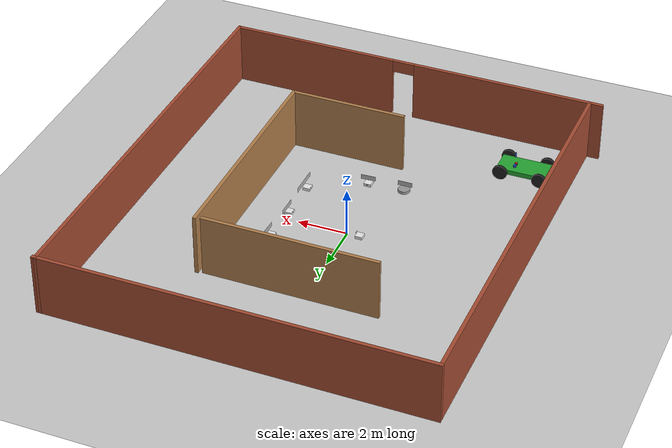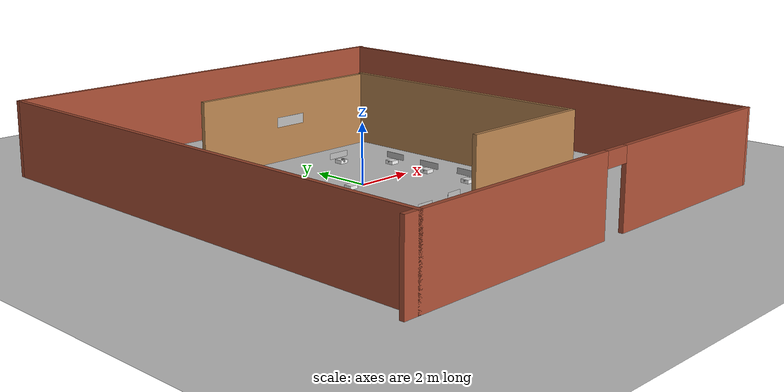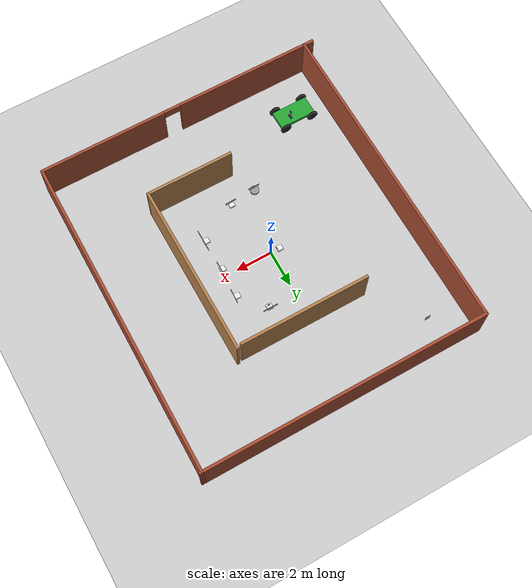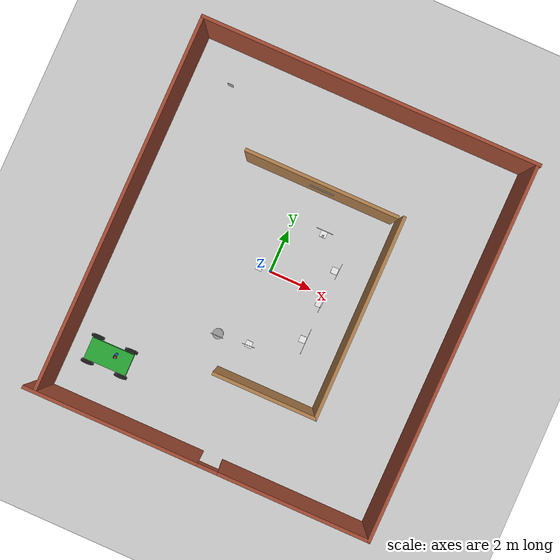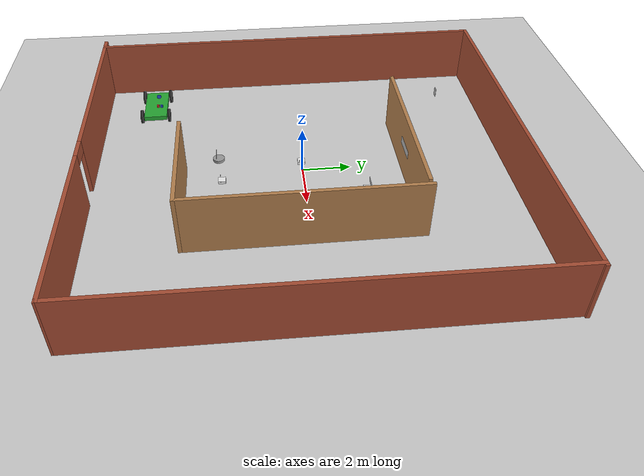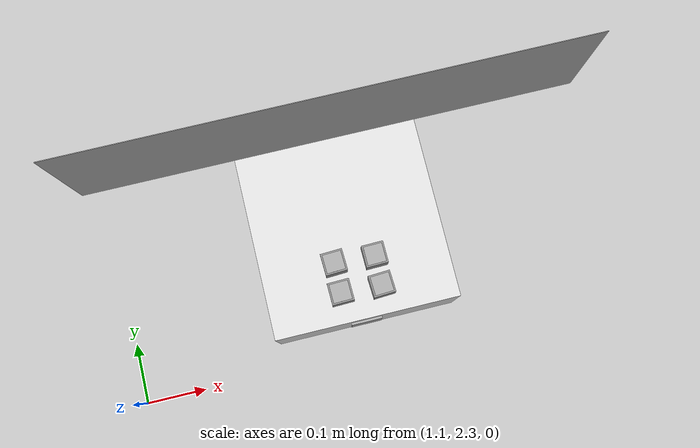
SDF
<sdf version="1.6">
 <world name="default">
  <light name="sun" type="directional">
   <pose>0 0 10 0 -0 0</pose>
   <diffuse>0.8 0.8 0.8 1</diffuse>
   <specular>0.1 0.1 0.1 1</specular>
   <attenuation>
    <range>1000</range>
    <constant>0.9</constant>
    <linear>0.01</linear>
    <quadratic>0.001</quadratic>
   </attenuation>
   <direction>-0.5 0.5 -1</direction>
  </light>
  <model name="ground_plane">
   <static>1</static>
   <link name="link">
    <collision name="collision">
     <geometry><plane><normal>0 0 1</normal><size>100 100</size></plane></geometry>
     <surface><friction><ode><mu>100</mu><mu2>50</mu2></ode></friction></surface>
    </collision>
    <visual name="visual">
     <cast_shadows>0</cast_shadows>
     <geometry><plane><normal>0 0 1</normal><size>100 100</size></plane></geometry>
     <material>
      <script><uri>file://media/materials/scripts/gazebo.material</uri><name>Gazebo/Grey</name></script>
     </material>
    </visual>
   </link>
  </model>
  <gravity>0 0 -9.8</gravity>
  <magnetic_field>6e-06 2.3e-05 -4.2e-05</magnetic_field>
  <atmosphere type="adiabatic"/>
  <physics name="default_physics" default="0" type="ode">
   <max_step_size>0.001</max_step_size>
   <real_time_factor>1</real_time_factor>
   <real_time_update_rate>1000</real_time_update_rate>
  </physics>
  <scene><ambient>0.4 0.4 0.4 1</ambient><background>0.7 0.7 0.7 1</background><shadows>1</shadows></scene>
  <spherical_coordinates>
   <surface_model>EARTH_WGS84</surface_model>
   <latitude_deg>0</latitude_deg>
   <longitude_deg>0</longitude_deg>
   <elevation>0</elevation>
   <heading_deg>0</heading_deg>
  </spherical_coordinates>
  <model name="Untitled">
   <pose>0.603431 0.0078 0 0 -0 0</pose>
   <link name="Wall_15">
    <pose>-0.106136 -8.55 0 0 -0 0</pose>
    <visual name="Wall_15_Visual_0">
     <pose>-3.91595 0 1.25 0 -0 0</pose>
     <geometry><box><size>7.91811 0.15 2.5</size></box></geometry>
     <material>
      <script><uri>file://media/materials/scripts/gazebo.material</uri><name>Gazebo/Bricks</name></script>
      <ambient>1 1 1 1</ambient>
     </material>
    </visual>
    <collision name="Wall_15_Collision_0">
     <geometry><box><size>7.91811 0.15 2.5</size></box></geometry>
     <pose>-3.91595 0 1.25 0 -0 0</pose>
    </collision>
    <visual name="Wall_15_Visual_1">
     <pose>4.40905 0 1.25 0 -0 0</pose>
     <geometry><box><size>6.93189 0.15 2.5</size></box></geometry>
     <material>
      <script><uri>file://media/materials/scripts/gazebo.material</uri><name>Gazebo/Bricks</name></script>
      <ambient>1 1 1 1</ambient>
     </material>
    </visual>
    <collision name="Wall_15_Collision_1">
     <geometry><box><size>6.93189 0.15 2.5</size></box></geometry>
     <pose>4.40905 0 1.25 0 -0 0</pose>
    </collision>
    <visual name="Wall_15_Visual_2">
     <pose>0.493108 0 2.25 0 -0 0</pose>
     <geometry><box><size>0.9 0.15 0.5</size></box></geometry>
     <material>
      <script><uri>file://media/materials/scripts/gazebo.material</uri><name>Gazebo/Bricks</name></script>
      <ambient>1 1 1 1</ambient>
     </material>
    </visual>
    <collision name="Wall_15_Collision_2">
     <geometry><box><size>0.9 0.15 0.5</size></box></geometry>
     <pose>0.493108 0 2.25 0 -0 0</pose>
    </collision>
   </link>
   <link name="Wall_16">
    <collision name="Wall_16_Collision">
     <geometry><box><size>17.2513 0.15 2.5</size></box></geometry>
     <pose>0 0 1.25 0 -0 0</pose>
    </collision>
    <visual name="Wall_16_Visual">
     <pose>0 0 1.25 0 -0 0</pose>
     <geometry><box><size>17.2513 0.15 2.5</size></box></geometry>
     <material>
      <script><uri>file://media/materials/scripts/gazebo.material</uri><name>Gazebo/Bricks</name></script>
      <ambient>1 1 1 1</ambient>
     </material>
    </visual>
    <pose>7.76462 0 0 0 -0 1.56252</pose>
   </link>
   <link name="Wall_17">
    <collision name="Wall_17_Collision">
     <geometry><box><size>15.5 0.15 2.5</size></box></geometry>
     <pose>0 0 1.25 0 -0 0</pose>
    </collision>
    <visual name="Wall_17_Visual">
     <pose>0 0 1.25 0 -0 0</pose>
     <geometry><box><size>15.5 0.15 2.5</size></box></geometry>
     <material>
      <script><uri>file://media/materials/scripts/gazebo.material</uri><name>Gazebo/Bricks</name></script>
      <ambient>1 1 1 1</ambient>
     </material>
    </visual>
    <pose>0.231135 8.55 0 0 -0 3.14159</pose>
   </link>
   <link name="Wall_21">
    <collision name="Wall_21_Collision">
     <geometry><box><size>17.25 0.15 2.5</size></box></geometry>
     <pose>0 0 1.25 0 -0 0</pose>
    </collision>
    <visual name="Wall_21_Visual">
     <pose>0 0 1.25 0 -0 0</pose>
     <geometry><box><size>17.25 0.15 2.5</size></box></geometry>
     <material>
      <script><uri>file://media/materials/scripts/gazebo.material</uri><name>Gazebo/Bricks</name></script>
      <ambient>1 1 1 1</ambient>
     </material>
    </visual>
    <pose>-7.44386 0 0 0 0 -1.5708</pose>
   </link>
   <link name="Wall_23">
    <collision name="Wall_23_Collision">
     <geometry><box><size>9.25 0.15 2.5</size></box></geometry>
     <pose>0 0 1.25 0 -0 0</pose>
    </collision>
    <visual name="Wall_23_Visual">
     <pose>0 0 1.25 0 -0 0</pose>
     <geometry><box><size>9.25 0.15 2.5</size></box></geometry>
     <material>
      <script><uri>file://media/materials/scripts/gazebo.material</uri><name>Gazebo/Wood</name></script>
      <ambient>1 1 1 1</ambient>
     </material>
    </visual>
    <pose>3.6418 -0.302151 0 0 0 -1.5708</pose>
   </link>
   <link name="Wall_24">
    <collision name="Wall_24_Collision">
     <geometry><box><size>4.75 0.15 2.5</size></box></geometry>
     <pose>0 0 1.25 0 -0 0</pose>
    </collision>
    <visual name="Wall_24_Visual">
     <pose>0 0 1.25 0 -0 0</pose>
     <geometry><box><size>4.75 0.15 2.5</size></box></geometry>
     <material>
      <script><uri>file://media/materials/scripts/gazebo.material</uri><name>Gazebo/Wood</name></script>
      <ambient>1 1 1 1</ambient>
     </material>
    </visual>
    <pose>1.3418 -4.85215 0 0 -0 3.14159</pose>
   </link>
   <link name="Wall_26">
    <collision name="Wall_26_Collision">
     <geometry><box><size>7 0.15 2.5</size></box></geometry>
     <pose>0 0 1.25 0 -0 0</pose>
    </collision>
    <visual name="Wall_26_Visual">
     <pose>0 0 1.25 0 -0 0</pose>
     <geometry><box><size>7 0.15 2.5</size></box></geometry>
     <material>
      <script><uri>file://media/materials/scripts/gazebo.material</uri><name>Gazebo/Wood</name></script>
      <ambient>1 1 1 1</ambient>
     </material>
    </visual>
    <pose>-0.066232 4.17709 0 0 -0 3.14159</pose>
   </link>
   <static>1</static>
  </model>
  <model name="charge_pile">
   <link name="link_0">
    <pose>0.001175 0.064666 -0.007829 0 -0 0</pose>
    <inertial>
     <mass>1</mass>
     <inertia>
      <ixx>0.166667</ixx>
      <ixy>0</ixy>
      <ixz>0</ixz>
      <iyy>0.166667</iyy>
      <iyz>0</iyz>
      <izz>0.166667</izz>
     </inertia>
    </inertial>
    <visual name="visual">
     <geometry><box><size>0.3 0.3 0.12</size></box></geometry>
     <material>
      <lighting>1</lighting>
      <script><uri>file://media/materials/scripts/gazebo.material</uri><name>Gazebo/White</name></script>
      <ambient>0.3 0.3 0.3 1</ambient>
      <diffuse>0.7 0.7 0.7 1</diffuse>
      <specular>0.01 0.01 0.01 1</specular>
      <emissive>0 0 0 1</emissive>
      <shader type="vertex"><normal_map>__default__</normal_map></shader>
     </material>
    </visual>
    <collision name="collision">
     <geometry><box><size>0.3 0.3 0.12</size></box></geometry>
     <surface>
      <friction>
       <ode><mu>1000</mu><mu2>1000</mu2><fdir1>0 0 0</fdir1><slip1>0</slip1><slip2>0</slip2></ode>
       <torsional>
        <coefficient>1</coefficient>
        <patch_radius>0</patch_radius>
        <surface_radius>0</surface_radius>
        <use_patch_radius>1</use_patch_radius>
        <ode><slip>0</slip></ode>
       </torsional>
      </friction>
      <bounce><restitution_coefficient>0</restitution_coefficient><threshold>1e+06</threshold></bounce>
      <contact>
       <collide_without_contact>0</collide_without_contact>
       <collide_without_contact_bitmask>1</collide_without_contact_bitmask>
       <collide_bitmask>1</collide_bitmask>
       <ode>
        <soft_cfm>0</soft_cfm>
        <soft_erp>0.2</soft_erp>
        <kp>1e+13</kp>
        <kd>1</kd>
        <max_vel>0.01</max_vel>
        <min_depth>0</min_depth>
       </ode>
       <bullet>
        <split_impulse>1</split_impulse>
        <split_impulse_penetration_threshold>-0.01</split_impulse_penetration_threshold>
        <soft_cfm>0</soft_cfm>
        <soft_erp>0.2</soft_erp>
        <kp>1e+13</kp>
        <kd>1</kd>
       </bullet>
      </contact>
     </surface>
    </collision>
   </link>
   <model name="ar_box0_50">
    <link name="link_0">
     <inertial>
      <mass>1.87342e-05</mass>
      <inertia>
       <ixx>9.25984e-08</ixx>
       <ixy>0</ixy>
       <ixz>0</ixz>
       <iyy>1.0155e-07</iyy>
       <iyz>0</iyz>
       <izz>1.22113e-07</izz>
      </inertia>
     </inertial>
     <visual name="visual">
      <geometry><box><size>0.05 0.05 0.05</size></box></geometry>
      <material>
       <lighting>1</lighting>
       <script>
        <uri>model://ar_box0_50/materials/scripts</uri>
        <uri>model://ar_box0_50/materials/textures</uri>
        <name>ArBox050/Image</name>
       </script>
       <ambient>0.3 0.3 0.3 1</ambient>
       <diffuse>0.7 0.7 0.7 1</diffuse>
       <specular>0.01 0.01 0.01 1</specular>
       <emissive>0 0 0 1</emissive>
      </material>
      <cast_shadows>0</cast_shadows>
     </visual>
     <collision name="collision">
      <geometry><box><size>0.05 0.05 0.05</size></box></geometry>
      <surface>
       <friction>
        <ode><mu>100</mu><mu2>100</mu2><fdir1>0 0 0</fdir1><slip1>0</slip1><slip2>0</slip2></ode>
        <torsional>
         <coefficient>1</coefficient>
         <patch_radius>0</patch_radius>
         <surface_radius>0</surface_radius>
         <use_patch_radius>1</use_patch_radius>
         <ode><slip>0</slip></ode>
        </torsional>
       </friction>
       <bounce><restitution_coefficient>0</restitution_coefficient><threshold>1e+06</threshold></bounce>
       <contact>
        <collide_without_contact>0</collide_without_contact>
        <collide_without_contact_bitmask>1</collide_without_contact_bitmask>
        <collide_bitmask>1</collide_bitmask>
        <ode>
         <soft_cfm>0</soft_cfm>
         <soft_erp>0.2</soft_erp>
         <kp>1e+13</kp>
         <kd>1</kd>
         <max_vel>0.01</max_vel>
         <min_depth>0</min_depth>
        </ode>
        <bullet>
         <split_impulse>1</split_impulse>
         <split_impulse_penetration_threshold>-0.01</split_impulse_penetration_threshold>
         <soft_cfm>0</soft_cfm>
         <soft_erp>0.2</soft_erp>
         <kp>1e+13</kp>
         <kd>1</kd>
        </bullet>
       </contact>
      </surface>
     </collision>
    </link>
    <static>0</static>
    <pose>-0.001175 -0.064151 0.007829 0 -0 0</pose>
   </model>
   <joint name="link_0_JOINT_0" type="fixed">
    <parent>link_0</parent>
    <child>ar_box0_50::link_0</child>
    <physics>
     <ode><limit><cfm>0</cfm><erp>0.2</erp></limit><suspension><cfm>0</cfm><erp>0.2</erp></suspension></ode>
    </physics>
   </joint>
   <static>0</static>
   <pose>-0.457807 -0.00142 0.067829 0 -0 1.56608</pose>
  </model>
  <model name="charge_pile_0">
   <link name="link_0">
    <pose>0.001175 0.064666 -0.007829 0 -0 0</pose>
    <inertial>
     <mass>1</mass>
     <inertia>
      <ixx>0.166667</ixx>
      <ixy>0</ixy>
      <ixz>0</ixz>
      <iyy>0.166667</iyy>
      <iyz>0</iyz>
      <izz>0.166667</izz>
     </inertia>
    </inertial>
    <visual name="visual">
     <geometry><box><size>0.3 0.3 0.12</size></box></geometry>
     <material>
      <lighting>1</lighting>
      <script><uri>file://media/materials/scripts/gazebo.material</uri><name>Gazebo/White</name></script>
      <ambient>0.3 0.3 0.3 1</ambient>
      <diffuse>0.7 0.7 0.7 1</diffuse>
      <specular>0.01 0.01 0.01 1</specular>
      <emissive>0 0 0 1</emissive>
      <shader type="vertex"><normal_map>__default__</normal_map></shader>
     </material>
    </visual>
    <collision name="collision">
     <geometry><box><size>0.3 0.3 0.12</size></box></geometry>
     <surface>
      <friction>
       <ode><mu>1000</mu><mu2>1000</mu2><fdir1>0 0 0</fdir1><slip1>0</slip1><slip2>0</slip2></ode>
       <torsional>
        <coefficient>1</coefficient>
        <patch_radius>0</patch_radius>
        <surface_radius>0</surface_radius>
        <use_patch_radius>1</use_patch_radius>
        <ode><slip>0</slip></ode>
       </torsional>
      </friction>
      <bounce><restitution_coefficient>0</restitution_coefficient><threshold>1e+06</threshold></bounce>
      <contact>
       <collide_without_contact>0</collide_without_contact>
       <collide_without_contact_bitmask>1</collide_without_contact_bitmask>
       <collide_bitmask>1</collide_bitmask>
       <ode>
        <soft_cfm>0</soft_cfm>
        <soft_erp>0.2</soft_erp>
        <kp>1e+13</kp>
        <kd>1</kd>
        <max_vel>0.01</max_vel>
        <min_depth>0</min_depth>
       </ode>
       <bullet>
        <split_impulse>1</split_impulse>
        <split_impulse_penetration_threshold>-0.01</split_impulse_penetration_threshold>
        <soft_cfm>0</soft_cfm>
        <soft_erp>0.2</soft_erp>
        <kp>1e+13</kp>
        <kd>1</kd>
       </bullet>
      </contact>
     </surface>
    </collision>
   </link>
   <model name="ar_box0_50">
    <link name="link_0">
     <inertial>
      <mass>1.87342e-05</mass>
      <inertia>
       <ixx>9.25984e-08</ixx>
       <ixy>0</ixy>
       <ixz>0</ixz>
       <iyy>1.0155e-07</iyy>
       <iyz>0</iyz>
       <izz>1.22113e-07</izz>
      </inertia>
     </inertial>
     <visual name="visual">
      <geometry><box><size>0.05 0.05 0.05</size></box></geometry>
      <material>
       <lighting>1</lighting>
       <script>
        <uri>model://ar_box0_50/materials/scripts</uri>
        <uri>model://ar_box0_50/materials/textures</uri>
        <name>ArBox050/Image</name>
       </script>
       <ambient>0.3 0.3 0.3 1</ambient>
       <diffuse>0.7 0.7 0.7 1</diffuse>
       <specular>0.01 0.01 0.01 1</specular>
       <emissive>0 0 0 1</emissive>
      </material>
      <cast_shadows>0</cast_shadows>
     </visual>
     <collision name="collision">
      <geometry><box><size>0.05 0.05 0.05</size></box></geometry>
      <surface>
       <friction>
        <ode><mu>100</mu><mu2>100</mu2><fdir1>0 0 0</fdir1><slip1>0</slip1><slip2>0</slip2></ode>
        <torsional>
         <coefficient>1</coefficient>
         <patch_radius>0</patch_radius>
         <surface_radius>0</surface_radius>
         <use_patch_radius>1</use_patch_radius>
         <ode><slip>0</slip></ode>
        </torsional>
       </friction>
       <bounce><restitution_coefficient>0</restitution_coefficient><threshold>1e+06</threshold></bounce>
       <contact>
        <collide_without_contact>0</collide_without_contact>
        <collide_without_contact_bitmask>1</collide_without_contact_bitmask>
        <collide_bitmask>1</collide_bitmask>
        <ode>
         <soft_cfm>0</soft_cfm>
         <soft_erp>0.2</soft_erp>
         <kp>1e+13</kp>
         <kd>1</kd>
         <max_vel>0.01</max_vel>
         <min_depth>0</min_depth>
        </ode>
        <bullet>
         <split_impulse>1</split_impulse>
         <split_impulse_penetration_threshold>-0.01</split_impulse_penetration_threshold>
         <soft_cfm>0</soft_cfm>
         <soft_erp>0.2</soft_erp>
         <kp>1e+13</kp>
         <kd>1</kd>
        </bullet>
       </contact>
      </surface>
     </collision>
    </link>
    <static>0</static>
    <pose>-0.001175 -0.064151 0.007829 0 -0 0</pose>
   </model>
   <joint name="link_0_JOINT_0" type="fixed">
    <parent>link_0</parent>
    <child>ar_box0_50::link_0</child>
    <physics>
     <ode><limit><cfm>0</cfm><erp>0.2</erp></limit><suspension><cfm>0</cfm><erp>0.2</erp></suspension></ode>
    </physics>
   </joint>
   <static>0</static>
   <pose>1.48811 2.43027 0.067829 0 -1e-06 0.00331</pose>
  </model>
  <model name="car">
   <link name="chassis">
    <pose>0 0 0.3 0 -0 0</pose>
    <collision name="collision"><geometry><box><size>2 1 0.2</size></box></geometry></collision>
    <visual name="visual">
     <geometry><box><size>2 1 0.2</size></box></geometry>
     <material>
      <script><uri>file://media/materials/scripts/gazebo.material</uri><name>Gazebo/Green</name></script>
     </material>
    </visual>
    <inertial>
     <inertia><ixx>1</ixx><ixy>0</ixy><ixz>0</ixz><iyy>1</iyy><iyz>0</iyz><izz>1</izz></inertia>
     <mass>1</mass>
    </inertial>
   </link>
   <link name="front_left_wheel">
    <pose>0.8 0.6 0.3 -0 1.5707 1.5707</pose>
    <collision name="collision">
     <geometry><cylinder><radius>0.3</radius><length>0.1</length></cylinder></geometry>
    </collision>
    <visual name="visual">
     <geometry><cylinder><radius>0.3</radius><length>0.1</length></cylinder></geometry>
     <material>
      <script><uri>file://media/materials/scripts/gazebo.material</uri><name>Gazebo/Black</name></script>
     </material>
    </visual>
    <inertial>
     <inertia><ixx>1</ixx><ixy>0</ixy><ixz>0</ixz><iyy>1</iyy><iyz>0</iyz><izz>1</izz></inertia>
     <mass>1</mass>
    </inertial>
   </link>
   <link name="front_right_wheel">
    <pose>0.8 -0.6 0.3 -0 1.5707 1.5707</pose>
    <collision name="collision">
     <geometry><cylinder><radius>0.3</radius><length>0.1</length></cylinder></geometry>
    </collision>
    <visual name="visual">
     <geometry><cylinder><radius>0.3</radius><length>0.1</length></cylinder></geometry>
     <material>
      <script><uri>file://media/materials/scripts/gazebo.material</uri><name>Gazebo/Black</name></script>
     </material>
    </visual>
    <inertial>
     <inertia><ixx>1</ixx><ixy>0</ixy><ixz>0</ixz><iyy>1</iyy><iyz>0</iyz><izz>1</izz></inertia>
     <mass>1</mass>
    </inertial>
   </link>
   <link name="back_right_wheel">
    <pose>-0.8 -0.6 0.3 -0 1.5707 1.5707</pose>
    <collision name="collision">
     <geometry><cylinder><radius>0.3</radius><length>0.1</length></cylinder></geometry>
    </collision>
    <visual name="visual">
     <geometry><cylinder><radius>0.3</radius><length>0.1</length></cylinder></geometry>
     <material>
      <script><uri>file://media/materials/scripts/gazebo.material</uri><name>Gazebo/Black</name></script>
     </material>
    </visual>
    <inertial>
     <inertia><ixx>1</ixx><ixy>0</ixy><ixz>0</ixz><iyy>1</iyy><iyz>0</iyz><izz>1</izz></inertia>
     <mass>1</mass>
    </inertial>
   </link>
   <link name="back_left_wheel">
    <pose>-0.8 0.6 0.3 -0 1.5707 1.5707</pose>
    <collision name="collision">
     <geometry><cylinder><radius>0.3</radius><length>0.1</length></cylinder></geometry>
    </collision>
    <visual name="visual">
     <geometry><cylinder><radius>0.3</radius><length>0.1</length></cylinder></geometry>
     <material>
      <script><uri>file://media/materials/scripts/gazebo.material</uri><name>Gazebo/Black</name></script>
     </material>
    </visual>
    <inertial>
     <inertia><ixx>1</ixx><ixy>0</ixy><ixz>0</ixz><iyy>1</iyy><iyz>0</iyz><izz>1</izz></inertia>
     <mass>1</mass>
    </inertial>
   </link>
   <link name="gas_pedal">
    <pose>0.3 0.1 0.5 0 -0 0</pose>
    <collision name="collision"><geometry><box><size>0.1 0.1 0.1</size></box></geometry></collision>
    <visual name="visual">
     <geometry><box><size>0.1 0.1 0.1</size></box></geometry>
     <material>
      <script><uri>file://media/materials/scripts/gazebo.material</uri><name>Gazebo/Red</name></script>
     </material>
    </visual>
    <inertial>
     <inertia><ixx>1</ixx><ixy>0</ixy><ixz>0</ixz><iyy>1</iyy><iyz>0</iyz><izz>1</izz></inertia>
     <mass>1</mass>
    </inertial>
   </link>
   <link name="brake_pedal">
    <pose>0.3 0.25 0.5 0 -0 0</pose>
    <collision name="collision"><geometry><box><size>0.1 0.1 0.1</size></box></geometry></collision>
    <visual name="visual">
     <geometry><box><size>0.1 0.1 0.1</size></box></geometry>
     <material>
      <script><uri>file://media/materials/scripts/gazebo.material</uri><name>Gazebo/Blue</name></script>
     </material>
    </visual>
    <inertial>
     <inertia><ixx>1</ixx><ixy>0</ixy><ixz>0</ixz><iyy>1</iyy><iyz>0</iyz><izz>1</izz></inertia>
     <mass>1</mass>
    </inertial>
   </link>
   <link name="steering_wheel">
    <pose>0.3 0.2 1 0 1.5707 0</pose>
    <collision name="collision">
     <geometry><cylinder><radius>0.1</radius><length>0.01</length></cylinder></geometry>
    </collision>
    <visual name="visual">
     <geometry><cylinder><radius>0.1</radius><length>0.01</length></cylinder></geometry>
     <material>
      <script><uri>file://media/materials/scripts/gazebo.material</uri><name>Gazebo/Blue</name></script>
     </material>
    </visual>
    <inertial>
     <inertia><ixx>1</ixx><ixy>0</ixy><ixz>0</ixz><iyy>1</iyy><iyz>0</iyz><izz>1</izz></inertia>
     <mass>1</mass>
    </inertial>
   </link>
   <joint name="gas_joint" type="prismatic">
    <parent>chassis</parent>
    <child>gas_pedal</child>
    <axis>
     <xyz>1 0 0</xyz>
     <limit><lower>0</lower><upper>0.2</upper></limit>
     <use_parent_model_frame>1</use_parent_model_frame>
     <dynamics><spring_reference>0</spring_reference><spring_stiffness>0</spring_stiffness></dynamics>
    </axis>
   </joint>
   <joint name="brake_joint" type="prismatic">
    <parent>chassis</parent>
    <child>brake_pedal</child>
    <axis>
     <xyz>1 0 0</xyz>
     <limit><lower>0</lower><upper>0.2</upper></limit>
     <use_parent_model_frame>1</use_parent_model_frame>
     <dynamics><spring_reference>0</spring_reference><spring_stiffness>0</spring_stiffness></dynamics>
    </axis>
   </joint>
   <joint name="steering_joint" type="revolute">
    <parent>chassis</parent>
    <child>steering_wheel</child>
    <axis>
     <xyz>1 0 0</xyz>
     <limit><lower>-7.853</lower><upper>7.853</upper></limit>
     <use_parent_model_frame>1</use_parent_model_frame>
     <dynamics><spring_reference>0</spring_reference><spring_stiffness>0</spring_stiffness></dynamics>
    </axis>
   </joint>
   <joint name="front_left_joint" type="revolute2">
    <parent>chassis</parent>
    <child>front_left_wheel</child>
    <axis>
     <xyz>0 0 1</xyz>
     <limit><lower>5.61641e-07</lower><upper>5.61641e-07</upper></limit>
     <use_parent_model_frame>1</use_parent_model_frame>
     <dynamics><spring_reference>0</spring_reference><spring_stiffness>0</spring_stiffness></dynamics>
    </axis>
    <axis2>
     <xyz>0 1 0</xyz>
     <use_parent_model_frame>1</use_parent_model_frame>
     <dynamics><spring_reference>0</spring_reference><spring_stiffness>0</spring_stiffness></dynamics>
    </axis2>
    <physics><ode><limit><cfm>0</cfm><erp>0.9</erp></limit></ode></physics>
   </joint>
   <joint name="front_right_joint" type="revolute2">
    <parent>chassis</parent>
    <child>front_right_wheel</child>
    <axis>
     <xyz>0 0 1</xyz>
     <limit><lower>5.61641e-07</lower><upper>5.61641e-07</upper></limit>
     <use_parent_model_frame>1</use_parent_model_frame>
     <dynamics><spring_reference>0</spring_reference><spring_stiffness>0</spring_stiffness></dynamics>
    </axis>
    <axis2>
     <xyz>0 1 0</xyz>
     <use_parent_model_frame>1</use_parent_model_frame>
     <dynamics><spring_reference>0</spring_reference><spring_stiffness>0</spring_stiffness></dynamics>
    </axis2>
    <physics><ode><limit><cfm>0</cfm><erp>0.9</erp></limit></ode></physics>
   </joint>
   <joint name="back_right_joint" type="revolute2">
    <parent>chassis</parent>
    <child>back_right_wheel</child>
    <axis>
     <xyz>0 0 1</xyz>
     <limit><lower>0</lower><upper>0</upper></limit>
     <use_parent_model_frame>1</use_parent_model_frame>
     <dynamics><spring_reference>0</spring_reference><spring_stiffness>0</spring_stiffness></dynamics>
    </axis>
    <axis2>
     <xyz>0 1 0</xyz>
     <use_parent_model_frame>1</use_parent_model_frame>
     <dynamics><spring_reference>0</spring_reference><spring_stiffness>0</spring_stiffness></dynamics>
    </axis2>
    <physics><ode><limit><cfm>0</cfm><erp>0.9</erp></limit></ode></physics>
   </joint>
   <joint name="back_left_joint" type="revolute2">
    <parent>chassis</parent>
    <child>back_left_wheel</child>
    <axis>
     <xyz>0 0 1</xyz>
     <limit><lower>0</lower><upper>0</upper></limit>
     <use_parent_model_frame>1</use_parent_model_frame>
     <dynamics><spring_reference>0</spring_reference><spring_stiffness>0</spring_stiffness></dynamics>
    </axis>
    <axis2>
     <xyz>0 1 0</xyz>
     <use_parent_model_frame>1</use_parent_model_frame>
     <dynamics><spring_reference>0</spring_reference><spring_stiffness>0</spring_stiffness></dynamics>
    </axis2>
    <physics><ode><limit><cfm>0</cfm><erp>0.9</erp></limit></ode></physics>
   </joint>
   <plugin name="vehicle" filename="libVehiclePlugin.so">
    <front_left>front_left_joint</front_left>
    <front_right>front_right_joint</front_right>
    <back_left>back_left_joint</back_left>
    <back_right>back_right_joint</back_right>
    <gas>gas_joint</gas>
    <brake>brake_joint</brake>
    <steering>steering_joint</steering>
    <front_power>10</front_power>
    <rear_power>10</rear_power>
    <tire_angle_range>0.5</tire_angle_range>
    <max_speed>10</max_speed>
    <aero_load>0.1</aero_load>
   </plugin>
   <pose>-4.96763 -6.30056 -0.002615 -0.000273 0.000908 0.006388</pose>
  </model>
  <model name="bobac">
   <link name="link_0">
    <inertial>
     <mass>1</mass>
     <inertia>
      <ixx>0.166667</ixx>
      <ixy>0</ixy>
      <ixz>0</ixz>
      <iyy>0.166667</iyy>
      <iyz>0</iyz>
      <izz>0.166667</izz>
     </inertia>
    </inertial>
    <visual name="visual">
     <geometry><box><size>0.268 0.01 0.399999</size></box></geometry>
     <material>
      <lighting>1</lighting>
      <script>
       <uri>model://bobac/materials/scripts</uri>
       <uri>model://bobac/materials/textures</uri>
       <name>Bobac/Image</name>
      </script>
      <ambient>0.3 0.3 0.3 1</ambient>
      <diffuse>0.7 0.7 0.7 1</diffuse>
      <specular>0.01 0.01 0.01 1</specular>
      <emissive>0 0 0 1</emissive>
      <shader type="vertex"><normal_map>__default__</normal_map></shader>
     </material>
    </visual>
    <collision name="collision">
     <geometry><box><size>0.0010002 0.001 0.000999449</size></box></geometry>
     <surface>
      <friction>
       <ode><mu>1</mu><mu2>1</mu2><fdir1>0 0 0</fdir1><slip1>0</slip1><slip2>0</slip2></ode>
       <torsional>
        <coefficient>1</coefficient>
        <patch_radius>0</patch_radius>
        <surface_radius>0</surface_radius>
        <use_patch_radius>1</use_patch_radius>
        <ode><slip>0</slip></ode>
       </torsional>
      </friction>
      <bounce><restitution_coefficient>0</restitution_coefficient><threshold>1e+06</threshold></bounce>
      <contact>
       <collide_without_contact>0</collide_without_contact>
       <collide_without_contact_bitmask>1</collide_without_contact_bitmask>
       <collide_bitmask>1</collide_bitmask>
       <ode>
        <soft_cfm>0</soft_cfm>
        <soft_erp>0.2</soft_erp>
        <kp>1e+13</kp>
        <kd>1</kd>
        <max_vel>0.01</max_vel>
        <min_depth>0</min_depth>
       </ode>
       <bullet>
        <split_impulse>1</split_impulse>
        <split_impulse_penetration_threshold>-0.01</split_impulse_penetration_threshold>
        <soft_cfm>0</soft_cfm>
        <soft_erp>0.2</soft_erp>
        <kp>1e+13</kp>
        <kd>1</kd>
       </bullet>
      </contact>
     </surface>
    </collision>
   </link>
   <static>1</static>
   <pose>-4.98574 6.88032 0.262723 0 -0 0</pose>
  </model>
  <model name="charge_flag">
   <link name="link_0">
    <inertial>
     <mass>1</mass>
     <inertia>
      <ixx>0.166667</ixx>
      <ixy>0</ixy>
      <ixz>0</ixz>
      <iyy>0.166667</iyy>
      <iyz>0</iyz>
      <izz>0.166667</izz>
     </inertia>
    </inertial>
    <visual name="visual">
     <geometry><box><size>0.165 0.001 0.094</size></box></geometry>
     <material>
      <lighting>1</lighting>
      <script>
       <uri>model://charge_flag/materials/scripts</uri>
       <uri>model://charge_flag/materials/textures</uri>
       <name>Charge/Image</name>
      </script>
      <ambient>0.3 0.3 0.3 1</ambient>
      <diffuse>0.7 0.7 0.7 1</diffuse>
      <specular>0.01 0.01 0.01 1</specular>
      <emissive>0 0 0 1</emissive>
      <shader type="vertex"><normal_map>__default__</normal_map></shader>
     </material>
    </visual>
    <collision name="collision">
     <geometry><box><size>0.001 0.001 0.001</size></box></geometry>
     <surface>
      <friction>
       <ode><mu>1</mu><mu2>1</mu2><fdir1>0 0 0</fdir1><slip1>0</slip1><slip2>0</slip2></ode>
       <torsional>
        <coefficient>1</coefficient>
        <patch_radius>0</patch_radius>
        <surface_radius>0</surface_radius>
        <use_patch_radius>1</use_patch_radius>
        <ode><slip>0</slip></ode>
       </torsional>
      </friction>
      <bounce><restitution_coefficient>0</restitution_coefficient><threshold>1e+06</threshold></bounce>
      <contact>
       <collide_without_contact>0</collide_without_contact>
       <collide_without_contact_bitmask>1</collide_without_contact_bitmask>
       <collide_bitmask>1</collide_bitmask>
       <ode>
        <soft_cfm>0</soft_cfm>
        <soft_erp>0.2</soft_erp>
        <kp>1e+13</kp>
        <kd>1</kd>
        <max_vel>0.01</max_vel>
        <min_depth>0</min_depth>
       </ode>
       <bullet>
        <split_impulse>1</split_impulse>
        <split_impulse_penetration_threshold>-0.01</split_impulse_penetration_threshold>
        <soft_cfm>0</soft_cfm>
        <soft_erp>0.2</soft_erp>
        <kp>1e+13</kp>
        <kd>1</kd>
       </bullet>
      </contact>
     </surface>
    </collision>
   </link>
   <static>1</static>
   <pose>-0.379743 -0.002865 0.1681 0 -0 1.57994</pose>
  </model>
  <model name="Textdepot">
   <link name="link_0">
    <inertial>
     <mass>1</mass>
     <inertia>
      <ixx>0.166667</ixx>
      <ixy>0</ixy>
      <ixz>0</ixz>
      <iyy>0.166667</iyy>
      <iyz>0</iyz>
      <izz>0.166667</izz>
     </inertia>
    </inertial>
    <visual name="visual">
     <geometry><box><size>0.799997 0.001 0.2</size></box></geometry>
     <material>
      <lighting>1</lighting>
      <script>
       <uri>model://Text/materials/scripts</uri>
       <uri>model://Text/materials/textures</uri>
       <name>Depot/Image</name>
      </script>
      <ambient>0.3 0.3 0.3 1</ambient>
      <diffuse>0.7 0.7 0.7 1</diffuse>
      <specular>0.01 0.01 0.01 1</specular>
      <emissive>0 0 0 1</emissive>
      <shader type="vertex"><normal_map>__default__</normal_map></shader>
     </material>
    </visual>
    <collision name="collision">
     <geometry><box><size>0.000999982 0.001 0.000999956</size></box></geometry>
     <surface>
      <friction>
       <ode><mu>1</mu><mu2>1</mu2><fdir1>0 0 0</fdir1><slip1>0</slip1><slip2>0</slip2></ode>
       <torsional>
        <coefficient>1</coefficient>
        <patch_radius>0</patch_radius>
        <surface_radius>0</surface_radius>
        <use_patch_radius>1</use_patch_radius>
        <ode><slip>0</slip></ode>
       </torsional>
      </friction>
      <bounce><restitution_coefficient>0</restitution_coefficient><threshold>1e+06</threshold></bounce>
      <contact>
       <collide_without_contact>0</collide_without_contact>
       <collide_without_contact_bitmask>1</collide_without_contact_bitmask>
       <collide_bitmask>1</collide_bitmask>
       <ode>
        <soft_cfm>0</soft_cfm>
        <soft_erp>0.2</soft_erp>
        <kp>1e+13</kp>
        <kd>1</kd>
        <max_vel>0.01</max_vel>
        <min_depth>0</min_depth>
       </ode>
       <bullet>
        <split_impulse>1</split_impulse>
        <split_impulse_penetration_threshold>-0.01</split_impulse_penetration_threshold>
        <soft_cfm>0</soft_cfm>
        <soft_erp>0.2</soft_erp>
        <kp>1e+13</kp>
        <kd>1</kd>
       </bullet>
      </contact>
     </surface>
    </collision>
   </link>
   <static>1</static>
   <pose>1.49576 2.63584 0.246075 0 -0 0</pose>
  </model>
  <model name="charge_pile_2">
   <link name="link_0">
    <pose>0.001175 0.064666 -0.007829 0 -0 0</pose>
    <inertial>
     <mass>1</mass>
     <inertia>
      <ixx>0.166667</ixx>
      <ixy>0</ixy>
      <ixz>0</ixz>
      <iyy>0.166667</iyy>
      <iyz>0</iyz>
      <izz>0.166667</izz>
     </inertia>
    </inertial>
    <visual name="visual">
     <geometry><box><size>0.3 0.3 0.12</size></box></geometry>
     <material>
      <lighting>1</lighting>
      <script><uri>file://media/materials/scripts/gazebo.material</uri><name>Gazebo/White</name></script>
      <ambient>0.3 0.3 0.3 1</ambient>
      <diffuse>0.7 0.7 0.7 1</diffuse>
      <specular>0.01 0.01 0.01 1</specular>
      <emissive>0 0 1 1</emissive>
      <shader type="vertex"><normal_map>__default__</normal_map></shader>
     </material>
    </visual>
    <collision name="collision">
     <geometry><box><size>0.3 0.3 0.12</size></box></geometry>
     <surface>
      <friction><ode><mu>100</mu><mu2>50</mu2></ode></friction>
      <bounce><restitution_coefficient>0</restitution_coefficient><threshold>1e+06</threshold></bounce>
      <contact>
       <collide_without_contact>0</collide_without_contact>
       <collide_without_contact_bitmask>1</collide_without_contact_bitmask>
       <collide_bitmask>1</collide_bitmask>
       <ode>
        <soft_cfm>0</soft_cfm>
        <soft_erp>0.2</soft_erp>
        <kp>1e+13</kp>
        <kd>1</kd>
        <max_vel>0.01</max_vel>
        <min_depth>0</min_depth>
       </ode>
       <bullet>
        <split_impulse>1</split_impulse>
        <split_impulse_penetration_threshold>-0.01</split_impulse_penetration_threshold>
        <soft_cfm>0</soft_cfm>
        <soft_erp>0.2</soft_erp>
        <kp>1e+13</kp>
        <kd>1</kd>
       </bullet>
      </contact>
     </surface>
    </collision>
   </link>
   <model name="ar_box0_50">
    <link name="link_0">
     <inertial>
      <mass>1.87342e-05</mass>
      <inertia>
       <ixx>9.25984e-08</ixx>
       <ixy>0</ixy>
       <ixz>0</ixz>
       <iyy>1.0155e-07</iyy>
       <iyz>0</iyz>
       <izz>1.22113e-07</izz>
      </inertia>
     </inertial>
     <visual name="visual">
      <geometry><box><size>0.05 0.05 0.05</size></box></geometry>
      <material>
       <lighting>1</lighting>
       <script>
        <uri>model://ar_box0_50/materials/scripts</uri>
        <uri>model://ar_box0_50/materials/textures</uri>
        <name>ArBox050/Image</name>
       </script>
       <ambient>0.3 0.3 0.3 1</ambient>
       <diffuse>0.7 0.7 0.7 1</diffuse>
       <specular>0.01 0.01 0.01 1</specular>
       <emissive>1 1 1 1</emissive>
      </material>
      <cast_shadows>0</cast_shadows>
     </visual>
     <collision name="collision">
      <geometry><box><size>0.05 0.05 0.05</size></box></geometry>
      <surface>
       <friction><ode><mu>100</mu><mu2>50</mu2></ode></friction>
       <bounce><restitution_coefficient>0</restitution_coefficient><threshold>1e+06</threshold></bounce>
       <contact>
        <collide_without_contact>0</collide_without_contact>
        <collide_without_contact_bitmask>1</collide_without_contact_bitmask>
        <collide_bitmask>1</collide_bitmask>
        <ode>
         <soft_cfm>0</soft_cfm>
         <soft_erp>0.2</soft_erp>
         <kp>1e+13</kp>
         <kd>1</kd>
         <max_vel>0.01</max_vel>
         <min_depth>0</min_depth>
        </ode>
        <bullet>
         <split_impulse>1</split_impulse>
         <split_impulse_penetration_threshold>-0.01</split_impulse_penetration_threshold>
         <soft_cfm>0</soft_cfm>
         <soft_erp>0.2</soft_erp>
         <kp>1e+13</kp>
         <kd>1</kd>
        </bullet>
       </contact>
      </surface>
     </collision>
    </link>
    <static>0</static>
    <pose>-0.001175 -0.064151 0.007829 0 -0 0</pose>
   </model>
   <joint name="link_0_JOINT_0" type="fixed">
    <parent>link_0</parent>
    <child>ar_box0_50::link_0</child>
    <physics>
     <ode><limit><cfm>0</cfm><erp>0.2</erp></limit><suspension><cfm>0</cfm><erp>0.2</erp></suspension></ode>
    </physics>
   </joint>
   <static>0</static>
   <pose>2.54114 1.20841 0.067829 0 0 -1.57555</pose>
  </model>
  <model name="Textcnc">
   <link name="link_0">
    <inertial>
     <mass>1</mass>
     <inertia>
      <ixx>0.166667</ixx>
      <ixy>0</ixy>
      <ixz>0</ixz>
      <iyy>0.166667</iyy>
      <iyz>0</iyz>
      <izz>0.166667</izz>
     </inertia>
    </inertial>
    <visual name="visual">
     <geometry><box><size>0.800001 0.001 0.2</size></box></geometry>
     <material>
      <lighting>1</lighting>
      <script>
       <uri>model://Text/materials/scripts</uri>
       <uri>model://Text/materials/textures</uri>
       <name>Cnc/Image</name>
      </script>
      <ambient>0.3 0.3 0.3 1</ambient>
      <diffuse>0.7 0.7 0.7 1</diffuse>
      <specular>0.01 0.01 0.01 1</specular>
      <emissive>0 0 0 1</emissive>
      <shader type="vertex"><normal_map>__default__</normal_map></shader>
     </material>
    </visual>
    <collision name="collision">
     <geometry><box><size>0.00100006 0.001 0.00100008</size></box></geometry>
     <surface>
      <friction>
       <ode><mu>1</mu><mu2>1</mu2><fdir1>0 0 0</fdir1><slip1>0</slip1><slip2>0</slip2></ode>
       <torsional>
        <coefficient>1</coefficient>
        <patch_radius>0</patch_radius>
        <surface_radius>0</surface_radius>
        <use_patch_radius>1</use_patch_radius>
        <ode><slip>0</slip></ode>
       </torsional>
      </friction>
      <bounce><restitution_coefficient>0</restitution_coefficient><threshold>1e+06</threshold></bounce>
      <contact>
       <collide_without_contact>0</collide_without_contact>
       <collide_without_contact_bitmask>1</collide_without_contact_bitmask>
       <collide_bitmask>1</collide_bitmask>
       <ode>
        <soft_cfm>0</soft_cfm>
        <soft_erp>0.2</soft_erp>
        <kp>1e+13</kp>
        <kd>1</kd>
        <max_vel>0.01</max_vel>
        <min_depth>0</min_depth>
       </ode>
       <bullet>
        <split_impulse>1</split_impulse>
        <split_impulse_penetration_threshold>-0.01</split_impulse_penetration_threshold>
        <soft_cfm>0</soft_cfm>
        <soft_erp>0.2</soft_erp>
        <kp>1e+13</kp>
        <kd>1</kd>
       </bullet>
      </contact>
     </surface>
    </collision>
   </link>
   <static>1</static>
   <pose>2.77965 1.20875 0.22821 0.000135 -0.008735 -1.61913</pose>
  </model>
  <model name="charge_pile_3">
   <link name="link_0">
    <pose>0.001175 0.064666 -0.007829 0 -0 0</pose>
    <inertial>
     <mass>1</mass>
     <inertia>
      <ixx>0.166667</ixx>
      <ixy>0</ixy>
      <ixz>0</ixz>
      <iyy>0.166667</iyy>
      <iyz>0</iyz>
      <izz>0.166667</izz>
     </inertia>
    </inertial>
    <visual name="visual">
     <geometry><box><size>0.3 0.3 0.12</size></box></geometry>
     <material>
      <lighting>1</lighting>
      <script><uri>file://media/materials/scripts/gazebo.material</uri><name>Gazebo/White</name></script>
      <ambient>0.3 0.3 0.3 1</ambient>
      <diffuse>0.7 0.7 0.7 1</diffuse>
      <specular>0.01 0.01 0.01 1</specular>
      <emissive>0 0 1 1</emissive>
      <shader type="vertex"><normal_map>__default__</normal_map></shader>
     </material>
    </visual>
    <collision name="collision">
     <geometry><box><size>0.3 0.3 0.12</size></box></geometry>
     <surface>
      <friction><ode><mu>100</mu><mu2>50</mu2></ode></friction>
      <bounce><restitution_coefficient>0</restitution_coefficient><threshold>1e+06</threshold></bounce>
      <contact>
       <collide_without_contact>0</collide_without_contact>
       <collide_without_contact_bitmask>1</collide_without_contact_bitmask>
       <collide_bitmask>1</collide_bitmask>
       <ode>
        <soft_cfm>0</soft_cfm>
        <soft_erp>0.2</soft_erp>
        <kp>1e+13</kp>
        <kd>1</kd>
        <max_vel>0.01</max_vel>
        <min_depth>0</min_depth>
       </ode>
       <bullet>
        <split_impulse>1</split_impulse>
        <split_impulse_penetration_threshold>-0.01</split_impulse_penetration_threshold>
        <soft_cfm>0</soft_cfm>
        <soft_erp>0.2</soft_erp>
        <kp>1e+13</kp>
        <kd>1</kd>
       </bullet>
      </contact>
     </surface>
    </collision>
   </link>
   <model name="ar_box0_50">
    <link name="link_0">
     <inertial>
      <mass>1.87342e-05</mass>
      <inertia>
       <ixx>9.25984e-08</ixx>
       <ixy>0</ixy>
       <ixz>0</ixz>
       <iyy>1.0155e-07</iyy>
       <iyz>0</iyz>
       <izz>1.22113e-07</izz>
      </inertia>
     </inertial>
     <visual name="visual">
      <geometry><box><size>0.05 0.05 0.05</size></box></geometry>
      <material>
       <lighting>1</lighting>
       <script>
        <uri>model://ar_box0_50/materials/scripts</uri>
        <uri>model://ar_box0_50/materials/textures</uri>
        <name>ArBox050/Image</name>
       </script>
       <ambient>0.3 0.3 0.3 1</ambient>
       <diffuse>0.7 0.7 0.7 1</diffuse>
       <specular>0.01 0.01 0.01 1</specular>
       <emissive>1 1 1 1</emissive>
      </material>
      <cast_shadows>0</cast_shadows>
     </visual>
     <collision name="collision">
      <geometry><box><size>0.05 0.05 0.05</size></box></geometry>
      <surface>
       <friction><ode><mu>100</mu><mu2>50</mu2></ode></friction>
       <bounce><restitution_coefficient>0</restitution_coefficient><threshold>1e+06</threshold></bounce>
       <contact>
        <collide_without_contact>0</collide_without_contact>
        <collide_without_contact_bitmask>1</collide_without_contact_bitmask>
        <collide_bitmask>1</collide_bitmask>
        <ode>
         <soft_cfm>0</soft_cfm>
         <soft_erp>0.2</soft_erp>
         <kp>1e+13</kp>
         <kd>1</kd>
         <max_vel>0.01</max_vel>
         <min_depth>0</min_depth>
        </ode>
        <bullet>
         <split_impulse>1</split_impulse>
         <split_impulse_penetration_threshold>-0.01</split_impulse_penetration_threshold>
         <soft_cfm>0</soft_cfm>
         <soft_erp>0.2</soft_erp>
         <kp>1e+13</kp>
         <kd>1</kd>
        </bullet>
       </contact>
      </surface>
     </collision>
    </link>
    <static>0</static>
    <pose>-0.001175 -0.064151 0.007829 0 -0 0</pose>
   </model>
   <joint name="link_0_JOINT_0" type="fixed">
    <parent>link_0</parent>
    <child>ar_box0_50::link_0</child>
    <physics>
     <ode><limit><cfm>0</cfm><erp>0.2</erp></limit><suspension><cfm>0</cfm><erp>0.2</erp></suspension></ode>
    </physics>
   </joint>
   <static>0</static>
   <pose>2.49613 -0.413245 0.067829 0 0 -1.57087</pose>
  </model>
  <model name="Text-AO">
   <link name="link_0">
    <inertial>
     <mass>1</mass>
     <inertia>
      <ixx>0.166667</ixx>
      <ixy>0</ixy>
      <ixz>0</ixz>
      <iyy>0.166667</iyy>
      <iyz>0</iyz>
      <izz>0.166667</izz>
     </inertia>
    </inertial>
    <visual name="visual">
     <geometry><box><size>1.2 0.001 0.2</size></box></geometry>
     <material>
      <lighting>1</lighting>
      <script>
       <uri>model://Text/materials/scripts</uri>
       <uri>model://Text/materials/textures</uri>
       <name>AO/Image</name>
      </script>
      <ambient>0.3 0.3 0.3 1</ambient>
      <diffuse>0.7 0.7 0.7 1</diffuse>
      <specular>0.01 0.01 0.01 1</specular>
      <emissive>0 0 0 1</emissive>
      <shader type="vertex"><normal_map>__default__</normal_map></shader>
     </material>
    </visual>
    <collision name="collision">
     <geometry><box><size>0.000998022 0.001 0.00100008</size></box></geometry>
     <surface>
      <friction>
       <ode><mu>1</mu><mu2>1</mu2><fdir1>0 0 0</fdir1><slip1>0</slip1><slip2>0</slip2></ode>
       <torsional>
        <coefficient>1</coefficient>
        <patch_radius>0</patch_radius>
        <surface_radius>0</surface_radius>
        <use_patch_radius>1</use_patch_radius>
        <ode><slip>0</slip></ode>
       </torsional>
      </friction>
      <bounce><restitution_coefficient>0</restitution_coefficient><threshold>1e+06</threshold></bounce>
      <contact>
       <collide_without_contact>0</collide_without_contact>
       <collide_without_contact_bitmask>1</collide_without_contact_bitmask>
       <collide_bitmask>1</collide_bitmask>
       <ode>
        <soft_cfm>0</soft_cfm>
        <soft_erp>0.2</soft_erp>
        <kp>1e+13</kp>
        <kd>1</kd>
        <max_vel>0.01</max_vel>
        <min_depth>0</min_depth>
       </ode>
       <bullet>
        <split_impulse>1</split_impulse>
        <split_impulse_penetration_threshold>-0.01</split_impulse_penetration_threshold>
        <soft_cfm>0</soft_cfm>
        <soft_erp>0.2</soft_erp>
        <kp>1e+13</kp>
        <kd>1</kd>
       </bullet>
      </contact>
     </surface>
    </collision>
   </link>
   <static>1</static>
   <pose>2.70061 -2.18044 0.252037 0 0 -1.57407</pose>
  </model>
  <model name="charge_pile_4">
   <link name="link_0">
    <pose>0.001175 0.064666 -0.007829 0 -0 0</pose>
    <inertial>
     <mass>1</mass>
     <inertia>
      <ixx>0.166667</ixx>
      <ixy>0</ixy>
      <ixz>0</ixz>
      <iyy>0.166667</iyy>
      <iyz>0</iyz>
      <izz>0.166667</izz>
     </inertia>
    </inertial>
    <visual name="visual">
     <geometry><box><size>0.3 0.3 0.12</size></box></geometry>
     <material>
      <lighting>1</lighting>
      <script><uri>file://media/materials/scripts/gazebo.material</uri><name>Gazebo/White</name></script>
      <ambient>0.3 0.3 0.3 1</ambient>
      <diffuse>0.7 0.7 0.7 1</diffuse>
      <specular>0.01 0.01 0.01 1</specular>
      <emissive>0 0 1 1</emissive>
      <shader type="vertex"><normal_map>__default__</normal_map></shader>
     </material>
    </visual>
    <collision name="collision">
     <geometry><box><size>0.3 0.3 0.12</size></box></geometry>
     <surface>
      <friction><ode><mu>100</mu><mu2>50</mu2></ode></friction>
      <bounce><restitution_coefficient>0</restitution_coefficient><threshold>1e+06</threshold></bounce>
      <contact>
       <collide_without_contact>0</collide_without_contact>
       <collide_without_contact_bitmask>1</collide_without_contact_bitmask>
       <collide_bitmask>1</collide_bitmask>
       <ode>
        <soft_cfm>0</soft_cfm>
        <soft_erp>0.2</soft_erp>
        <kp>1e+13</kp>
        <kd>1</kd>
        <max_vel>0.01</max_vel>
        <min_depth>0</min_depth>
       </ode>
       <bullet>
        <split_impulse>1</split_impulse>
        <split_impulse_penetration_threshold>-0.01</split_impulse_penetration_threshold>
        <soft_cfm>0</soft_cfm>
        <soft_erp>0.2</soft_erp>
        <kp>1e+13</kp>
        <kd>1</kd>
       </bullet>
      </contact>
     </surface>
    </collision>
   </link>
   <model name="ar_box0_50">
    <link name="link_0">
     <inertial>
      <mass>1.87342e-05</mass>
      <inertia>
       <ixx>9.25984e-08</ixx>
       <ixy>0</ixy>
       <ixz>0</ixz>
       <iyy>1.0155e-07</iyy>
       <iyz>0</iyz>
       <izz>1.22113e-07</izz>
      </inertia>
     </inertial>
     <visual name="visual">
      <geometry><box><size>0.05 0.05 0.05</size></box></geometry>
      <material>
       <lighting>1</lighting>
       <script>
        <uri>model://ar_box0_50/materials/scripts</uri>
        <uri>model://ar_box0_50/materials/textures</uri>
        <name>ArBox050/Image</name>
       </script>
       <ambient>0.3 0.3 0.3 1</ambient>
       <diffuse>0.7 0.7 0.7 1</diffuse>
       <specular>0.01 0.01 0.01 1</specular>
       <emissive>1 1 1 1</emissive>
      </material>
      <cast_shadows>0</cast_shadows>
     </visual>
     <collision name="collision">
      <geometry><box><size>0.05 0.05 0.05</size></box></geometry>
      <surface>
       <friction><ode><mu>100</mu><mu2>50</mu2></ode></friction>
       <bounce><restitution_coefficient>0</restitution_coefficient><threshold>1e+06</threshold></bounce>
       <contact>
        <collide_without_contact>0</collide_without_contact>
        <collide_without_contact_bitmask>1</collide_without_contact_bitmask>
        <collide_bitmask>1</collide_bitmask>
        <ode>
         <soft_cfm>0</soft_cfm>
         <soft_erp>0.2</soft_erp>
         <kp>1e+13</kp>
         <kd>1</kd>
         <max_vel>0.01</max_vel>
         <min_depth>0</min_depth>
        </ode>
        <bullet>
         <split_impulse>1</split_impulse>
         <split_impulse_penetration_threshold>-0.01</split_impulse_penetration_threshold>
         <soft_cfm>0</soft_cfm>
         <soft_erp>0.2</soft_erp>
         <kp>1e+13</kp>
         <kd>1</kd>
        </bullet>
       </contact>
      </surface>
     </collision>
    </link>
    <static>0</static>
    <pose>-0.001175 -0.064151 0.007829 0 -0 0</pose>
   </model>
   <joint name="link_0_JOINT_0" type="fixed">
    <parent>link_0</parent>
    <child>ar_box0_50::link_0</child>
    <physics>
     <ode><limit><cfm>0</cfm><erp>0.2</erp></limit><suspension><cfm>0</cfm><erp>0.2</erp></suspension></ode>
    </physics>
   </joint>
   <static>0</static>
   <pose>2.47722 -2.15716 0.067829 0 0 -1.56101</pose>
  </model>
  <model name="TextEndProduct">
   <link name="link_0">
    <inertial>
     <mass>1</mass>
     <inertia>
      <ixx>0.166667</ixx>
      <ixy>0</ixy>
      <ixz>0</ixz>
      <iyy>0.166667</iyy>
      <iyz>0</iyz>
      <izz>0.166667</izz>
     </inertia>
    </inertial>
    <visual name="visual">
     <geometry><box><size>0.599999 0.001 0.2</size></box></geometry>
     <material>
      <lighting>1</lighting>
      <script>
       <uri>model://Text/materials/scripts</uri>
       <uri>model://Text/materials/textures</uri>
       <name>EndProduct/Image</name>
      </script>
      <ambient>0.3 0.3 0.3 1</ambient>
      <diffuse>0.7 0.7 0.7 1</diffuse>
      <specular>0.01 0.01 0.01 1</specular>
      <emissive>0 0 0 1</emissive>
      <shader type="vertex"><normal_map>__default__</normal_map></shader>
     </material>
    </visual>
    <collision name="collision">
     <geometry><box><size>0.00099999 0.001 0.00100016</size></box></geometry>
     <surface>
      <friction>
       <ode><mu>1</mu><mu2>1</mu2><fdir1>0 0 0</fdir1><slip1>0</slip1><slip2>0</slip2></ode>
       <torsional>
        <coefficient>1</coefficient>
        <patch_radius>0</patch_radius>
        <surface_radius>0</surface_radius>
        <use_patch_radius>1</use_patch_radius>
        <ode><slip>0</slip></ode>
       </torsional>
      </friction>
      <bounce><restitution_coefficient>0</restitution_coefficient><threshold>1e+06</threshold></bounce>
      <contact>
       <collide_without_contact>0</collide_without_contact>
       <collide_without_contact_bitmask>1</collide_without_contact_bitmask>
       <collide_bitmask>1</collide_bitmask>
       <ode>
        <soft_cfm>0</soft_cfm>
        <soft_erp>0.2</soft_erp>
        <kp>1e+13</kp>
        <kd>1</kd>
        <max_vel>0.01</max_vel>
        <min_depth>0</min_depth>
       </ode>
       <bullet>
        <split_impulse>1</split_impulse>
        <split_impulse_penetration_threshold>-0.01</split_impulse_penetration_threshold>
        <soft_cfm>0</soft_cfm>
        <soft_erp>0.2</soft_erp>
        <kp>1e+13</kp>
        <kd>1</kd>
       </bullet>
      </contact>
     </surface>
    </collision>
   </link>
   <static>1</static>
   <pose>0.463313 -3.37499 0.285689 0 0 -3.09719</pose>
  </model>
  <model name="TextRecycle">
   <link name="link_0">
    <inertial>
     <mass>1</mass>
     <inertia>
      <ixx>0.166667</ixx>
      <ixy>0</ixy>
      <ixz>0</ixz>
      <iyy>0.166667</iyy>
      <iyz>0</iyz>
      <izz>0.166667</izz>
     </inertia>
    </inertial>
    <visual name="visual">
     <geometry><box><size>0.599998 0.001 0.199999</size></box></geometry>
     <material>
      <lighting>1</lighting>
      <script>
       <uri>model://Text/materials/scripts</uri>
       <uri>model://Text/materials/textures</uri>
       <name>Recycle/Image</name>
      </script>
      <ambient>0.3 0.3 0.3 1</ambient>
      <diffuse>0.7 0.7 0.7 1</diffuse>
      <specular>0.01 0.01 0.01 1</specular>
      <emissive>0 0 0 1</emissive>
      <shader type="vertex"><normal_map>__default__</normal_map></shader>
     </material>
    </visual>
    <collision name="collision">
     <geometry><box><size>0.00100116 0.001 0.000998926</size></box></geometry>
     <surface>
      <friction>
       <ode><mu>1</mu><mu2>1</mu2><fdir1>0 0 0</fdir1><slip1>0</slip1><slip2>0</slip2></ode>
       <torsional>
        <coefficient>1</coefficient>
        <patch_radius>0</patch_radius>
        <surface_radius>0</surface_radius>
        <use_patch_radius>1</use_patch_radius>
        <ode><slip>0</slip></ode>
       </torsional>
      </friction>
      <bounce><restitution_coefficient>0</restitution_coefficient><threshold>1e+06</threshold></bounce>
      <contact>
       <collide_without_contact>0</collide_without_contact>
       <collide_without_contact_bitmask>1</collide_without_contact_bitmask>
       <collide_bitmask>1</collide_bitmask>
       <ode>
        <soft_cfm>0</soft_cfm>
        <soft_erp>0.2</soft_erp>
        <kp>1e+13</kp>
        <kd>1</kd>
        <max_vel>0.01</max_vel>
        <min_depth>0</min_depth>
       </ode>
       <bullet>
        <split_impulse>1</split_impulse>
        <split_impulse_penetration_threshold>-0.01</split_impulse_penetration_threshold>
        <soft_cfm>0</soft_cfm>
        <soft_erp>0.2</soft_erp>
        <kp>1e+13</kp>
        <kd>1</kd>
       </bullet>
      </contact>
     </surface>
    </collision>
   </link>
   <static>1</static>
   <pose>-1.00963 -3.5438 0.277131 0 -0 0</pose>
  </model>
  <model name="Textcnc_0">
   <link name="link_0">
    <inertial>
     <mass>1</mass>
     <inertia>
      <ixx>0.166667</ixx>
      <ixy>0</ixy>
      <ixz>0</ixz>
      <iyy>0.166667</iyy>
      <iyz>0</iyz>
      <izz>0.166667</izz>
     </inertia>
    </inertial>
    <visual name="visual">
     <geometry><box><size>0.8 0.001 0.2</size></box></geometry>
     <material>
      <lighting>1</lighting>
      <script>
       <uri>model://Text/materials/scripts</uri>
       <uri>model://Text/materials/textures</uri>
       <name>Cnc/Image</name>
      </script>
      <ambient>0.3 0.3 0.3 1</ambient>
      <diffuse>0.7 0.7 0.7 1</diffuse>
      <specular>0.01 0.01 0.01 1</specular>
      <emissive>0 0 0 1</emissive>
      <shader type="vertex"><normal_map>__default__</normal_map></shader>
     </material>
    </visual>
    <collision name="collision">
     <geometry><box><size>0.001 0.001 0.001</size></box></geometry>
     <surface>
      <friction>
       <ode><mu>1</mu><mu2>1</mu2><fdir1>0 0 0</fdir1><slip1>0</slip1><slip2>0</slip2></ode>
       <torsional>
        <coefficient>1</coefficient>
        <patch_radius>0</patch_radius>
        <surface_radius>0</surface_radius>
        <use_patch_radius>1</use_patch_radius>
        <ode><slip>0</slip></ode>
       </torsional>
      </friction>
      <bounce><restitution_coefficient>0</restitution_coefficient><threshold>1e+06</threshold></bounce>
      <contact>
       <collide_without_contact>0</collide_without_contact>
       <collide_without_contact_bitmask>1</collide_without_contact_bitmask>
       <collide_bitmask>1</collide_bitmask>
       <ode>
        <soft_cfm>0</soft_cfm>
        <soft_erp>0.2</soft_erp>
        <kp>1e+13</kp>
        <kd>1</kd>
        <max_vel>0.01</max_vel>
        <min_depth>0</min_depth>
       </ode>
       <bullet>
        <split_impulse>1</split_impulse>
        <split_impulse_penetration_threshold>-0.01</split_impulse_penetration_threshold>
        <soft_cfm>0</soft_cfm>
        <soft_erp>0.2</soft_erp>
        <kp>1e+13</kp>
        <kd>1</kd>
       </bullet>
      </contact>
     </surface>
    </collision>
   </link>
   <static>1</static>
   <pose>2.66371 -0.420749 0.238218 0 0 -1.57548</pose>
  </model>
  <model name="charge_pile_5">
   <link name="link_0">
    <pose>0.001175 0.064666 -0.007829 0 -0 0</pose>
    <inertial>
     <mass>1</mass>
     <inertia>
      <ixx>0.166667</ixx>
      <ixy>0</ixy>
      <ixz>0</ixz>
      <iyy>0.166667</iyy>
      <iyz>0</iyz>
      <izz>0.166667</izz>
     </inertia>
    </inertial>
    <visual name="visual">
     <geometry><box><size>0.3 0.3 0.12</size></box></geometry>
     <material>
      <lighting>1</lighting>
      <script><uri>file://media/materials/scripts/gazebo.material</uri><name>Gazebo/White</name></script>
      <ambient>0.3 0.3 0.3 1</ambient>
      <diffuse>0.7 0.7 0.7 1</diffuse>
      <specular>0.01 0.01 0.01 1</specular>
      <emissive>0 0 1 1</emissive>
      <shader type="vertex"><normal_map>__default__</normal_map></shader>
     </material>
    </visual>
    <collision name="collision">
     <geometry><box><size>0.3 0.3 0.12</size></box></geometry>
     <surface>
      <friction><ode><mu>100</mu><mu2>50</mu2></ode></friction>
      <bounce><restitution_coefficient>0</restitution_coefficient><threshold>1e+06</threshold></bounce>
      <contact>
       <collide_without_contact>0</collide_without_contact>
       <collide_without_contact_bitmask>1</collide_without_contact_bitmask>
       <collide_bitmask>1</collide_bitmask>
       <ode>
        <soft_cfm>0</soft_cfm>
        <soft_erp>0.2</soft_erp>
        <kp>1e+13</kp>
        <kd>1</kd>
        <max_vel>0.01</max_vel>
        <min_depth>0</min_depth>
       </ode>
       <bullet>
        <split_impulse>1</split_impulse>
        <split_impulse_penetration_threshold>-0.01</split_impulse_penetration_threshold>
        <soft_cfm>0</soft_cfm>
        <soft_erp>0.2</soft_erp>
        <kp>1e+13</kp>
        <kd>1</kd>
       </bullet>
      </contact>
     </surface>
    </collision>
   </link>
   <model name="ar_box0_50">
    <link name="link_0">
     <inertial>
      <mass>1.87342e-05</mass>
      <inertia>
       <ixx>9.25984e-08</ixx>
       <ixy>0</ixy>
       <ixz>0</ixz>
       <iyy>1.0155e-07</iyy>
       <iyz>0</iyz>
       <izz>1.22113e-07</izz>
      </inertia>
     </inertial>
     <visual name="visual">
      <geometry><box><size>0.05 0.05 0.05</size></box></geometry>
      <material>
       <lighting>1</lighting>
       <script>
        <uri>model://ar_box0_50/materials/scripts</uri>
        <uri>model://ar_box0_50/materials/textures</uri>
        <name>ArBox050/Image</name>
       </script>
       <ambient>0.3 0.3 0.3 1</ambient>
       <diffuse>0.7 0.7 0.7 1</diffuse>
       <specular>0.01 0.01 0.01 1</specular>
       <emissive>1 1 1 1</emissive>
      </material>
      <cast_shadows>0</cast_shadows>
     </visual>
     <collision name="collision">
      <geometry><box><size>0.05 0.05 0.05</size></box></geometry>
      <surface>
       <friction><ode><mu>100</mu><mu2>50</mu2></ode></friction>
       <bounce><restitution_coefficient>0</restitution_coefficient><threshold>1e+06</threshold></bounce>
       <contact>
        <collide_without_contact>0</collide_without_contact>
        <collide_without_contact_bitmask>1</collide_without_contact_bitmask>
        <collide_bitmask>1</collide_bitmask>
        <ode>
         <soft_cfm>0</soft_cfm>
         <soft_erp>0.2</soft_erp>
         <kp>1e+13</kp>
         <kd>1</kd>
         <max_vel>0.01</max_vel>
         <min_depth>0</min_depth>
        </ode>
        <bullet>
         <split_impulse>1</split_impulse>
         <split_impulse_penetration_threshold>-0.01</split_impulse_penetration_threshold>
         <soft_cfm>0</soft_cfm>
         <soft_erp>0.2</soft_erp>
         <kp>1e+13</kp>
         <kd>1</kd>
        </bullet>
       </contact>
      </surface>
     </collision>
    </link>
    <static>0</static>
    <pose>-0.001175 -0.064151 0.007829 0 -0 0</pose>
   </model>
   <joint name="link_0_JOINT_0" type="fixed">
    <parent>link_0</parent>
    <child>ar_box0_50::link_0</child>
    <physics>
     <ode><limit><cfm>0</cfm><erp>0.2</erp></limit><suspension><cfm>0</cfm><erp>0.2</erp></suspension></ode>
    </physics>
   </joint>
   <static>0</static>
   <pose>0.442099 -3.25925 0.067829 0 -0 3.12796</pose>
  </model>
  <model name="yuanzhu">
   <link name="link_0">
    <inertial>
     <mass>1</mass>
     <inertia><ixx>0.145833</ixx><ixy>0</ixy><ixz>0</ixz><iyy>0.145833</iyy><iyz>0</iyz><izz>0.125</izz></inertia>
    </inertial>
    <visual name="visual">
     <geometry><cylinder><radius>0.241658</radius><length>0.118588</length></cylinder></geometry>
     <material>
      <lighting>1</lighting>
      <script><uri>file://media/materials/scripts/gazebo.material</uri><name>Gazebo/Grey</name></script>
      <ambient>0.3 0.3 0.3 1</ambient>
      <diffuse>0.7 0.7 0.7 1</diffuse>
      <specular>0.01 0.01 0.01 1</specular>
      <emissive>0 0 0 1</emissive>
     </material>
    </visual>
    <collision name="collision">
     <geometry><cylinder><radius>0.241658</radius><length>0.118588</length></cylinder></geometry>
     <surface>
      <friction>
       <ode><mu>1</mu><mu2>1</mu2><fdir1>0 0 0</fdir1><slip1>0</slip1><slip2>0</slip2></ode>
       <torsional>
        <coefficient>1</coefficient>
        <patch_radius>0</patch_radius>
        <surface_radius>0</surface_radius>
        <use_patch_radius>1</use_patch_radius>
        <ode><slip>0</slip></ode>
       </torsional>
      </friction>
      <bounce><restitution_coefficient>0</restitution_coefficient><threshold>1e+06</threshold></bounce>
      <contact>
       <collide_without_contact>0</collide_without_contact>
       <collide_without_contact_bitmask>1</collide_without_contact_bitmask>
       <collide_bitmask>1</collide_bitmask>
       <ode>
        <soft_cfm>0</soft_cfm>
        <soft_erp>0.2</soft_erp>
        <kp>1e+13</kp>
        <kd>1</kd>
        <max_vel>0.01</max_vel>
        <min_depth>0</min_depth>
       </ode>
       <bullet>
        <split_impulse>1</split_impulse>
        <split_impulse_penetration_threshold>-0.01</split_impulse_penetration_threshold>
        <soft_cfm>0</soft_cfm>
        <soft_erp>0.2</soft_erp>
        <kp>1e+13</kp>
        <kd>1</kd>
       </bullet>
      </contact>
     </surface>
    </collision>
   </link>
   <static>0</static>
   <pose>-1.00159 -3.45395 0.059288 -2e-06 -2e-06 0</pose>
  </model>
  <model name="reinovo">
   <link name="link_0">
    <inertial>
     <mass>1</mass>
     <inertia>
      <ixx>0.166667</ixx>
      <ixy>0</ixy>
      <ixz>0</ixz>
      <iyy>0.166667</iyy>
      <iyz>0</iyz>
      <izz>0.166667</izz>
     </inertia>
    </inertial>
    <visual name="visual">
     <geometry><box><size>1.15354 0.005 0.334517</size></box></geometry>
     <material>
      <lighting>1</lighting>
      <script>
       <uri>model://reinovo/materials/scripts</uri>
       <uri>model://reinovo/materials/textures</uri>
       <name>Reinovo/Image</name>
      </script>
      <ambient>0.3 0.3 0.3 1</ambient>
      <diffuse>0.7 0.7 0.7 1</diffuse>
      <specular>0.01 0.01 0.01 1</specular>
      <emissive>0 0 0 1</emissive>
      <shader type="vertex"><normal_map>__default__</normal_map></shader>
     </material>
    </visual>
    <collision name="collision">
     <geometry><box><size>0.0384513 0.01 0.0278764</size></box></geometry>
     <surface>
      <friction>
       <ode><mu>1</mu><mu2>1</mu2><fdir1>0 0 0</fdir1><slip1>0</slip1><slip2>0</slip2></ode>
       <torsional>
        <coefficient>1</coefficient>
        <patch_radius>0</patch_radius>
        <surface_radius>0</surface_radius>
        <use_patch_radius>1</use_patch_radius>
        <ode><slip>0</slip></ode>
       </torsional>
      </friction>
      <bounce><restitution_coefficient>0</restitution_coefficient><threshold>1e+06</threshold></bounce>
      <contact>
       <collide_without_contact>0</collide_without_contact>
       <collide_without_contact_bitmask>1</collide_without_contact_bitmask>
       <collide_bitmask>1</collide_bitmask>
       <ode>
        <soft_cfm>0</soft_cfm>
        <soft_erp>0.2</soft_erp>
        <kp>1e+13</kp>
        <kd>1</kd>
        <max_vel>0.01</max_vel>
        <min_depth>0</min_depth>
       </ode>
       <bullet>
        <split_impulse>1</split_impulse>
        <split_impulse_penetration_threshold>-0.01</split_impulse_penetration_threshold>
        <soft_cfm>0</soft_cfm>
        <soft_erp>0.2</soft_erp>
        <kp>1e+13</kp>
        <kd>1</kd>
       </bullet>
      </contact>
     </surface>
    </collision>
   </link>
   <static>1</static>
   <pose>0.635417 4.07811 1.35988 0 -0 0</pose>
  </model>
  <model name="ar_box1_one">
   <link name="link_0">
    <inertial>
     <mass>0.2</mass>
     <inertia>
      <ixx>0.166667</ixx>
      <ixy>0</ixy>
      <ixz>0</ixz>
      <iyy>0.166667</iyy>
      <iyz>0</iyz>
      <izz>0.166667</izz>
     </inertia>
    </inertial>
    <visual name="visual">
     <geometry><box><size>0.035 0.035 0.03</size></box></geometry>
     <material>
      <lighting>1</lighting>
      <script><uri>file://media/materials/scripts/gazebo.material</uri><name>Gazebo/Grey</name></script>
      <ambient>0.3 0.3 0.3 1</ambient>
      <diffuse>0.7 0.7 0.7 1</diffuse>
      <specular>0.01 0.01 0.01 1</specular>
      <emissive>1 1 1 1</emissive>
      <shader type="vertex"><normal_map>__default__</normal_map></shader>
     </material>
    </visual>
    <collision name="collision">
     <geometry><cylinder><radius>0.0214</radius><length>0.03</length></cylinder></geometry>
     <surface>
      <friction><ode><mu>0.2</mu><mu2>0.2</mu2></ode></friction>
      <bounce><restitution_coefficient>0</restitution_coefficient><threshold>1e+06</threshold></bounce>
      <contact>
       <collide_without_contact>0</collide_without_contact>
       <collide_without_contact_bitmask>1</collide_without_contact_bitmask>
       <collide_bitmask>1</collide_bitmask>
       <ode>
        <soft_cfm>0</soft_cfm>
        <soft_erp>0.2</soft_erp>
        <kp>1e+13</kp>
        <kd>1</kd>
        <max_vel>0.01</max_vel>
        <min_depth>0</min_depth>
       </ode>
       <bullet>
        <split_impulse>1</split_impulse>
        <split_impulse_penetration_threshold>-0.01</split_impulse_penetration_threshold>
        <soft_cfm>0</soft_cfm>
        <soft_erp>0.2</soft_erp>
        <kp>1e+13</kp>
        <kd>1</kd>
       </bullet>
      </contact>
     </surface>
    </collision>
   </link>
   <model name="ar_box1">
    <link name="link_0">
     <inertial>
      <mass>1.87342e-05</mass>
      <inertia>
       <ixx>9.25984e-08</ixx>
       <ixy>0</ixy>
       <ixz>0</ixz>
       <iyy>1.0155e-07</iyy>
       <iyz>0</iyz>
       <izz>1.22113e-07</izz>
      </inertia>
     </inertial>
     <visual name="visual">
      <geometry><box><size>0.0298 0.0298 0.0305</size></box></geometry>
      <material>
       <lighting>1</lighting>
       <script>
        <uri>model://ar_box1/materials/scripts</uri>
        <uri>model://ar_box1/materials/textures</uri>
        <name>ArBox1/Image</name>
       </script>
       <ambient>0.3 0.3 0.3 1</ambient>
       <diffuse>0.7 0.7 0.7 1</diffuse>
       <specular>0.01 0.01 0.01 1</specular>
       <emissive>1 1 1 1</emissive>
      </material>
      <cast_shadows>0</cast_shadows>
     </visual>
     <collision name="collision">
      <geometry><box><size>0.03 0.03 0.03</size></box></geometry>
      <surface>
       <friction><ode><mu>0.2</mu><mu2>0.2</mu2></ode></friction>
       <bounce><restitution_coefficient>0</restitution_coefficient><threshold>1e+06</threshold></bounce>
       <contact>
        <collide_without_contact>0</collide_without_contact>
        <collide_without_contact_bitmask>1</collide_without_contact_bitmask>
        <collide_bitmask>1</collide_bitmask>
        <ode>
         <soft_cfm>0</soft_cfm>
         <soft_erp>0.2</soft_erp>
         <kp>1e+13</kp>
         <kd>1</kd>
         <max_vel>0.01</max_vel>
         <min_depth>0</min_depth>
        </ode>
        <bullet>
         <split_impulse>1</split_impulse>
         <split_impulse_penetration_threshold>-0.01</split_impulse_penetration_threshold>
         <soft_cfm>0</soft_cfm>
         <soft_erp>0.2</soft_erp>
         <kp>1e+13</kp>
         <kd>1</kd>
        </bullet>
       </contact>
      </surface>
     </collision>
    </link>
    <static>0</static>
   </model>
   <joint name="link_0_JOINT_0" type="fixed">
    <parent>link_0</parent>
    <child>ar_box1::link_0</child>
    <physics>
     <ode><limit><cfm>0</cfm><erp>0.2</erp></limit><suspension><cfm>0</cfm><erp>0.2</erp></suspension></ode>
    </physics>
   </joint>
   <static>0</static>
   <pose>1.45643 2.3924 0.135005 3.14144 0.000167 -3.11364</pose>
  </model>
  <model name="ar_box2_one_0">
   <link name="link_0">
    <inertial>
     <mass>0.2</mass>
     <inertia>
      <ixx>0.166667</ixx>
      <ixy>0</ixy>
      <ixz>0</ixz>
      <iyy>0.166667</iyy>
      <iyz>0</iyz>
      <izz>0.166667</izz>
     </inertia>
    </inertial>
    <visual name="visual">
     <geometry><box><size>0.035 0.035 0.03</size></box></geometry>
     <material>
      <lighting>1</lighting>
      <script><uri>file://media/materials/scripts/gazebo.material</uri><name>Gazebo/Grey</name></script>
      <ambient>0.3 0.3 0.3 1</ambient>
      <diffuse>0.7 0.7 0.7 1</diffuse>
      <specular>0.01 0.01 0.01 1</specular>
      <emissive>1 1 1 1</emissive>
      <shader type="vertex"><normal_map>__default__</normal_map></shader>
     </material>
    </visual>
    <collision name="collision">
     <geometry><cylinder><radius>0.0214</radius><length>0.03</length></cylinder></geometry>
     <surface>
      <friction><ode><mu>1</mu><mu2>1</mu2></ode></friction>
      <bounce><restitution_coefficient>0</restitution_coefficient><threshold>1e+06</threshold></bounce>
      <contact>
       <collide_without_contact>0</collide_without_contact>
       <collide_without_contact_bitmask>1</collide_without_contact_bitmask>
       <collide_bitmask>1</collide_bitmask>
       <ode>
        <soft_cfm>0</soft_cfm>
        <soft_erp>0.2</soft_erp>
        <kp>1e+13</kp>
        <kd>1</kd>
        <max_vel>0.01</max_vel>
        <min_depth>0</min_depth>
       </ode>
       <bullet>
        <split_impulse>1</split_impulse>
        <split_impulse_penetration_threshold>-0.01</split_impulse_penetration_threshold>
        <soft_cfm>0</soft_cfm>
        <soft_erp>0.2</soft_erp>
        <kp>1e+13</kp>
        <kd>1</kd>
       </bullet>
      </contact>
     </surface>
    </collision>
   </link>
   <model name="ar_box2">
    <link name="link_0">
     <inertial>
      <mass>1.87342e-05</mass>
      <inertia>
       <ixx>9.25984e-08</ixx>
       <ixy>0</ixy>
       <ixz>0</ixz>
       <iyy>1.0155e-07</iyy>
       <iyz>0</iyz>
       <izz>1.22113e-07</izz>
      </inertia>
     </inertial>
     <visual name="visual">
      <geometry><box><size>0.0298 0.0298 0.0305</size></box></geometry>
      <material>
       <lighting>1</lighting>
       <script>
        <uri>model://ar_box2/materials/scripts</uri>
        <uri>model://ar_box2/materials/textures</uri>
        <name>ArBox2/Image</name>
       </script>
       <ambient>0.3 0.3 0.3 1</ambient>
       <diffuse>0.7 0.7 0.7 1</diffuse>
       <specular>0.01 0.01 0.01 1</specular>
       <emissive>1 1 1 1</emissive>
      </material>
      <cast_shadows>0</cast_shadows>
     </visual>
     <collision name="collision">
      <geometry><box><size>0.03 0.03 0.03</size></box></geometry>
      <surface>
       <friction><ode><mu>2</mu><mu2>2</mu2></ode></friction>
       <bounce><restitution_coefficient>0</restitution_coefficient><threshold>1e+06</threshold></bounce>
       <contact>
        <collide_without_contact>0</collide_without_contact>
        <collide_without_contact_bitmask>1</collide_without_contact_bitmask>
        <collide_bitmask>1</collide_bitmask>
        <ode>
         <soft_cfm>0</soft_cfm>
         <soft_erp>0.2</soft_erp>
         <kp>1e+13</kp>
         <kd>1</kd>
         <max_vel>0.01</max_vel>
         <min_depth>0</min_depth>
        </ode>
        <bullet>
         <split_impulse>1</split_impulse>
         <split_impulse_penetration_threshold>-0.01</split_impulse_penetration_threshold>
         <soft_cfm>0</soft_cfm>
         <soft_erp>0.2</soft_erp>
         <kp>1e+13</kp>
         <kd>1</kd>
        </bullet>
       </contact>
      </surface>
     </collision>
    </link>
    <static>0</static>
   </model>
   <joint name="link_0_JOINT_0" type="fixed">
    <parent>link_0</parent>
    <child>ar_box2::link_0</child>
    <physics>
     <ode><limit><cfm>0</cfm><erp>0.2</erp></limit><suspension><cfm>0</cfm><erp>0.2</erp></suspension></ode>
    </physics>
   </joint>
   <static>0</static>
   <pose>1.52156 2.43708 0.135008 3.1414 -0.000324 1.59346</pose>
  </model>
  <model name="ar_box3_one">
   <link name="link_0">
    <inertial>
     <mass>0.2</mass>
     <inertia>
      <ixx>0.166667</ixx>
      <ixy>0</ixy>
      <ixz>0</ixz>
      <iyy>0.166667</iyy>
      <iyz>0</iyz>
      <izz>0.166667</izz>
     </inertia>
    </inertial>
    <visual name="visual">
     <geometry><box><size>0.035 0.035 0.03</size></box></geometry>
     <material>
      <lighting>1</lighting>
      <script><uri>file://media/materials/scripts/gazebo.material</uri><name>Gazebo/Grey</name></script>
      <ambient>0.3 0.3 0.3 1</ambient>
      <diffuse>0.7 0.7 0.7 1</diffuse>
      <specular>0.01 0.01 0.01 1</specular>
      <emissive>1 1 1 1</emissive>
      <shader type="vertex"><normal_map>__default__</normal_map></shader>
     </material>
    </visual>
    <collision name="collision">
     <geometry><cylinder><radius>0.0214</radius><length>0.03</length></cylinder></geometry>
     <surface>
      <friction><ode><mu>0.2</mu><mu2>0.2</mu2></ode></friction>
      <bounce><restitution_coefficient>0</restitution_coefficient><threshold>1e+06</threshold></bounce>
      <contact>
       <collide_without_contact>0</collide_without_contact>
       <collide_without_contact_bitmask>1</collide_without_contact_bitmask>
       <collide_bitmask>1</collide_bitmask>
       <ode>
        <soft_cfm>0</soft_cfm>
        <soft_erp>0.2</soft_erp>
        <kp>1e+13</kp>
        <kd>1</kd>
        <max_vel>0.01</max_vel>
        <min_depth>0</min_depth>
       </ode>
       <bullet>
        <split_impulse>1</split_impulse>
        <split_impulse_penetration_threshold>-0.01</split_impulse_penetration_threshold>
        <soft_cfm>0</soft_cfm>
        <soft_erp>0.2</soft_erp>
        <kp>1e+13</kp>
        <kd>1</kd>
       </bullet>
      </contact>
     </surface>
    </collision>
   </link>
   <model name="ar_box3">
    <link name="link_0">
     <inertial>
      <mass>1.87342e-05</mass>
      <inertia>
       <ixx>9.25984e-08</ixx>
       <ixy>0</ixy>
       <ixz>0</ixz>
       <iyy>1.0155e-07</iyy>
       <iyz>0</iyz>
       <izz>1.22113e-07</izz>
      </inertia>
     </inertial>
     <visual name="visual">
      <geometry><box><size>0.0298 0.0298 0.0305</size></box></geometry>
      <material>
       <lighting>1</lighting>
       <script>
        <uri>model://ar_box3/materials/scripts</uri>
        <uri>model://ar_box3/materials/textures</uri>
        <name>ArBox3/Image</name>
       </script>
       <ambient>0.3 0.3 0.3 1</ambient>
       <diffuse>0.7 0.7 0.7 1</diffuse>
       <specular>0.01 0.01 0.01 1</specular>
       <emissive>1 1 1 1</emissive>
      </material>
      <cast_shadows>0</cast_shadows>
     </visual>
     <collision name="collision">
      <geometry><box><size>0.03 0.03 0.03</size></box></geometry>
      <surface>
       <friction><ode><mu>0.2</mu><mu2>0.2</mu2></ode></friction>
       <bounce><restitution_coefficient>0</restitution_coefficient><threshold>1e+06</threshold></bounce>
       <contact>
        <collide_without_contact>0</collide_without_contact>
        <collide_without_contact_bitmask>1</collide_without_contact_bitmask>
        <collide_bitmask>1</collide_bitmask>
        <ode>
         <soft_cfm>0</soft_cfm>
         <soft_erp>0.2</soft_erp>
         <kp>1e+13</kp>
         <kd>1</kd>
         <max_vel>0.01</max_vel>
         <min_depth>0</min_depth>
        </ode>
        <bullet>
         <split_impulse>1</split_impulse>
         <split_impulse_penetration_threshold>-0.01</split_impulse_penetration_threshold>
         <soft_cfm>0</soft_cfm>
         <soft_erp>0.2</soft_erp>
         <kp>1e+13</kp>
         <kd>1</kd>
        </bullet>
       </contact>
      </surface>
     </collision>
    </link>
    <static>0</static>
   </model>
   <joint name="link_0_JOINT_0" type="fixed">
    <parent>link_0</parent>
    <child>ar_box3::link_0</child>
    <physics>
     <ode><limit><cfm>0</cfm><erp>0.2</erp></limit><suspension><cfm>0</cfm><erp>0.2</erp></suspension></ode>
    </physics>
   </joint>
   <static>0</static>
   <pose>1.45685 2.43978 0.135007 3.1413 5.5e-05 -3.09314</pose>
  </model>
  <model name="ar_box4_one">
   <link name="link_0">
    <inertial>
     <mass>0.2</mass>
     <inertia>
      <ixx>0.166667</ixx>
      <ixy>0</ixy>
      <ixz>0</ixz>
      <iyy>0.166667</iyy>
      <iyz>0</iyz>
      <izz>0.166667</izz>
     </inertia>
    </inertial>
    <visual name="visual">
     <geometry><box><size>0.035 0.035 0.03</size></box></geometry>
     <material>
      <lighting>1</lighting>
      <script><uri>file://media/materials/scripts/gazebo.material</uri><name>Gazebo/Grey</name></script>
      <ambient>0.3 0.3 0.3 1</ambient>
      <diffuse>0.7 0.7 0.7 1</diffuse>
      <specular>0.01 0.01 0.01 1</specular>
      <emissive>1 1 1 1</emissive>
      <shader type="vertex"><normal_map>__default__</normal_map></shader>
     </material>
    </visual>
    <collision name="collision">
     <geometry><cylinder><radius>0.0214</radius><length>0.03</length></cylinder></geometry>
     <surface>
      <friction><ode><mu>0.2</mu><mu2>0.2</mu2></ode></friction>
      <bounce><restitution_coefficient>0</restitution_coefficient><threshold>1e+06</threshold></bounce>
      <contact>
       <collide_without_contact>0</collide_without_contact>
       <collide_without_contact_bitmask>1</collide_without_contact_bitmask>
       <collide_bitmask>1</collide_bitmask>
       <ode>
        <soft_cfm>0</soft_cfm>
        <soft_erp>0.2</soft_erp>
        <kp>1e+13</kp>
        <kd>1</kd>
        <max_vel>0.01</max_vel>
        <min_depth>0</min_depth>
       </ode>
       <bullet>
        <split_impulse>1</split_impulse>
        <split_impulse_penetration_threshold>-0.01</split_impulse_penetration_threshold>
        <soft_cfm>0</soft_cfm>
        <soft_erp>0.2</soft_erp>
        <kp>1e+13</kp>
        <kd>1</kd>
       </bullet>
      </contact>
     </surface>
    </collision>
   </link>
   <model name="ar_box4">
    <link name="link_0">
     <inertial>
      <mass>1.87342e-05</mass>
      <inertia>
       <ixx>9.25984e-08</ixx>
       <ixy>0</ixy>
       <ixz>0</ixz>
       <iyy>1.0155e-07</iyy>
       <iyz>0</iyz>
       <izz>1.22113e-07</izz>
      </inertia>
     </inertial>
     <visual name="visual">
      <geometry><box><size>0.0298 0.0298 0.0305</size></box></geometry>
      <material>
       <lighting>1</lighting>
       <script>
        <uri>model://ar_box4/materials/scripts</uri>
        <uri>model://ar_box4/materials/textures</uri>
        <name>ArBox4/Image</name>
       </script>
       <ambient>0.3 0.3 0.3 1</ambient>
       <diffuse>0.7 0.7 0.7 1</diffuse>
       <specular>0.01 0.01 0.01 1</specular>
       <emissive>1 1 1 1</emissive>
      </material>
      <cast_shadows>0</cast_shadows>
     </visual>
     <collision name="collision">
      <geometry><box><size>0.03 0.03 0.03</size></box></geometry>
      <surface>
       <friction><ode><mu>0.2</mu><mu2>0.2</mu2></ode></friction>
       <bounce><restitution_coefficient>0</restitution_coefficient><threshold>1e+06</threshold></bounce>
       <contact>
        <collide_without_contact>0</collide_without_contact>
        <collide_without_contact_bitmask>1</collide_without_contact_bitmask>
        <collide_bitmask>1</collide_bitmask>
        <ode>
         <soft_cfm>0</soft_cfm>
         <soft_erp>0.2</soft_erp>
         <kp>1e+13</kp>
         <kd>1</kd>
         <max_vel>0.01</max_vel>
         <min_depth>0</min_depth>
        </ode>
        <bullet>
         <split_impulse>1</split_impulse>
         <split_impulse_penetration_threshold>-0.01</split_impulse_penetration_threshold>
         <soft_cfm>0</soft_cfm>
         <soft_erp>0.2</soft_erp>
         <kp>1e+13</kp>
         <kd>1</kd>
        </bullet>
       </contact>
      </surface>
     </collision>
    </link>
    <static>0</static>
   </model>
   <joint name="link_0_JOINT_0" type="fixed">
    <parent>link_0</parent>
    <child>ar_box4::link_0</child>
    <physics>
     <ode><limit><cfm>0</cfm><erp>0.2</erp></limit><suspension><cfm>0</cfm><erp>0.2</erp></suspension></ode>
    </physics>
   </joint>
   <static>0</static>
   <pose>1.52136 2.38951 0.135005 3.14152 -0.000183 1.62757</pose>
  </model>
 </world>
</sdf>
